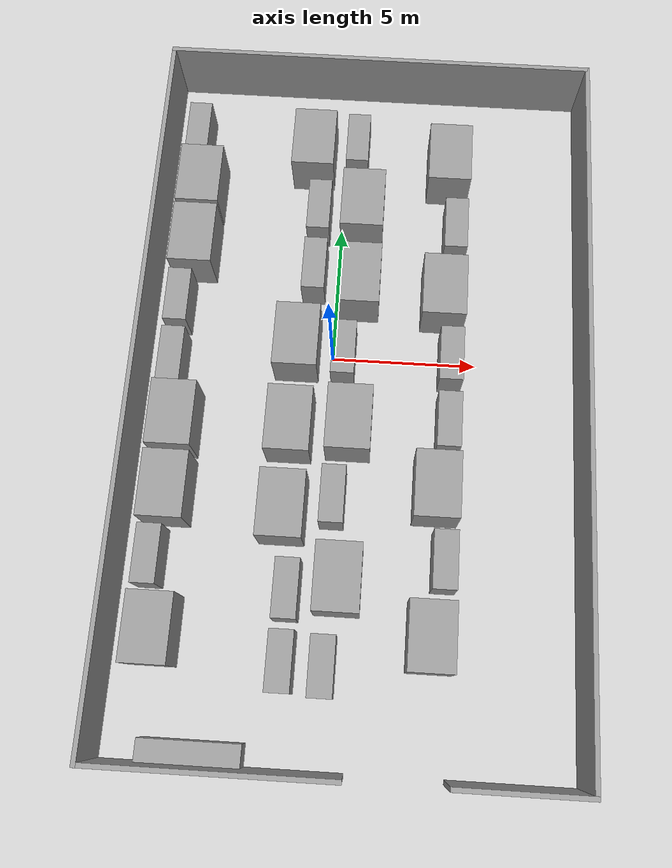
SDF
<sdf version="1.6">
 <world name="default">
  <light name="sun" type="directional">
   <pose>0 0 10 0 -0 0</pose>
   <diffuse>0.8 0.8 0.8 1</diffuse>
   <specular>0.1 0.1 0.1 1</specular>
   <attenuation>
    <range>1000</range>
    <constant>0.9</constant>
    <linear>0.01</linear>
    <quadratic>0.001</quadratic>
   </attenuation>
   <direction>-0.5 0.5 -1</direction>
  </light>
  <model name="ground_plane">
   <static>1</static>
   <link name="link">
    <collision name="collision">
     <geometry><plane><normal>0 0 1</normal><size>100 100</size></plane></geometry>
     <surface><friction><ode><mu>100</mu><mu2>50</mu2></ode></friction></surface>
    </collision>
    <visual name="visual">
     <cast_shadows>0</cast_shadows>
     <geometry><plane><normal>0 0 1</normal><size>100 100</size></plane></geometry>
     <material>
      <script><uri>file://media/materials/scripts/gazebo.material</uri><name>Gazebo/Grey</name></script>
     </material>
    </visual>
   </link>
  </model>
  <gravity>0 0 -9.8</gravity>
  <magnetic_field>6e-06 2.3e-05 -4.2e-05</magnetic_field>
  <atmosphere type="adiabatic"/>
  <physics name="default_physics" default="0" type="ode">
   <max_step_size>0.001</max_step_size>
   <real_time_factor>1</real_time_factor>
   <real_time_update_rate>1000</real_time_update_rate>
  </physics>
  <scene><ambient>0.4 0.4 0.4 1</ambient><background>0.7 0.7 0.7 1</background><shadows>1</shadows></scene>
  <spherical_coordinates>
   <surface_model>EARTH_WGS84</surface_model>
   <latitude_deg>0</latitude_deg>
   <longitude_deg>0</longitude_deg>
   <elevation>0</elevation>
   <heading_deg>0</heading_deg>
  </spherical_coordinates>
  <model name="Machine_08x19">
   <link name="link_1">
    <pose>0 0 0.95 0 -0 0</pose>
    <inertial>
     <mass>1000</mass>
     <inertia><ixx>488.333</ixx><ixy>0</ixy><ixz>0</ixz><iyy>240.833</iyy><iyz>0</iyz><izz>354.167</izz></inertia>
    </inertial>
    <visual name="visual">
     <geometry><box><size>0.8 1.9 1.5</size></box></geometry>
     <material>
      <lighting>1</lighting>
      <script><uri>file://media/materials/scripts/gazebo.material</uri><name>Gazebo/Grey</name></script>
      <ambient>0.3 0.3 0.3 1</ambient>
      <diffuse>0.7 0.7 0.7 1</diffuse>
      <specular>0.01 0.01 0.01 1</specular>
      <emissive>0 0 0 1</emissive>
      <shader type="vertex"><normal_map>__default__</normal_map></shader>
     </material>
    </visual>
    <collision name="collision">
     <geometry><box><size>0.8 1.9 1.5</size></box></geometry>
     <surface>
      <friction>
       <ode><mu>1</mu><mu2>1</mu2><fdir1>0 0 0</fdir1><slip1>0</slip1><slip2>0</slip2></ode>
       <torsional>
        <coefficient>1</coefficient>
        <patch_radius>0</patch_radius>
        <surface_radius>0</surface_radius>
        <use_patch_radius>1</use_patch_radius>
        <ode><slip>0</slip></ode>
       </torsional>
      </friction>
      <bounce><restitution_coefficient>0</restitution_coefficient><threshold>1e+06</threshold></bounce>
      <contact>
       <collide_without_contact>0</collide_without_contact>
       <collide_without_contact_bitmask>1</collide_without_contact_bitmask>
       <collide_bitmask>1</collide_bitmask>
       <ode>
        <soft_cfm>0</soft_cfm>
        <soft_erp>0.2</soft_erp>
        <kp>1e+13</kp>
        <kd>1</kd>
        <max_vel>0.01</max_vel>
        <min_depth>0</min_depth>
       </ode>
       <bullet>
        <split_impulse>1</split_impulse>
        <split_impulse_penetration_threshold>-0.01</split_impulse_penetration_threshold>
        <soft_cfm>0</soft_cfm>
        <soft_erp>0.2</soft_erp>
        <kp>1e+13</kp>
        <kd>1</kd>
       </bullet>
      </contact>
     </surface>
    </collision>
   </link>
   <static>0</static>
   <pose>0.405714 -0.010713 -0.2 0 -0 0</pose>
  </model>
  <model name="Machine_15x22">
   <link name="link_1">
    <inertial>
     <mass>1000</mass>
     <inertia><ixx>704.167</ixx><ixy>0</ixy><ixz>0</ixz><iyy>488.333</iyy><iyz>0</iyz><izz>590.833</izz></inertia>
    </inertial>
    <visual name="visual">
     <geometry><box><size>1.5 2.2 1.9</size></box></geometry>
     <material>
      <lighting>1</lighting>
      <script><uri>file://media/materials/scripts/gazebo.material</uri><name>Gazebo/Grey</name></script>
      <ambient>0.3 0.3 0.3 1</ambient>
      <diffuse>0.7 0.7 0.7 1</diffuse>
      <specular>0.01 0.01 0.01 1</specular>
      <emissive>0 0 0 1</emissive>
      <shader type="vertex"><normal_map>__default__</normal_map></shader>
     </material>
    </visual>
    <collision name="collision">
     <geometry><box><size>1.5 2.2 1.9</size></box></geometry>
     <surface>
      <friction>
       <ode><mu>1</mu><mu2>1</mu2><fdir1>0 0 0</fdir1><slip1>0</slip1><slip2>0</slip2></ode>
       <torsional>
        <coefficient>1</coefficient>
        <patch_radius>0</patch_radius>
        <surface_radius>0</surface_radius>
        <use_patch_radius>1</use_patch_radius>
        <ode><slip>0</slip></ode>
       </torsional>
      </friction>
      <bounce><restitution_coefficient>0</restitution_coefficient><threshold>1e+06</threshold></bounce>
      <contact>
       <collide_without_contact>0</collide_without_contact>
       <collide_without_contact_bitmask>1</collide_without_contact_bitmask>
       <collide_bitmask>1</collide_bitmask>
       <ode>
        <soft_cfm>0</soft_cfm>
        <soft_erp>0.2</soft_erp>
        <kp>1e+13</kp>
        <kd>1</kd>
        <max_vel>0.01</max_vel>
        <min_depth>0</min_depth>
       </ode>
       <bullet>
        <split_impulse>1</split_impulse>
        <split_impulse_penetration_threshold>-0.01</split_impulse_penetration_threshold>
        <soft_cfm>0</soft_cfm>
        <soft_erp>0.2</soft_erp>
        <kp>1e+13</kp>
        <kd>1</kd>
       </bullet>
      </contact>
     </surface>
    </collision>
   </link>
   <static>0</static>
   <pose>0.76024 2.59177 0.95 0 -0 0</pose>
  </model>
  <model name="Machine_15x22_clone">
   <link name="link_1">
    <inertial>
     <mass>1000</mass>
     <inertia><ixx>704.167</ixx><ixy>0</ixy><ixz>0</ixz><iyy>488.333</iyy><iyz>0</iyz><izz>590.833</izz></inertia>
    </inertial>
    <visual name="visual">
     <geometry><box><size>1.5 2.2 1.9</size></box></geometry>
     <material>
      <lighting>1</lighting>
      <script><uri>file://media/materials/scripts/gazebo.material</uri><name>Gazebo/Grey</name></script>
      <ambient>0.3 0.3 0.3 1</ambient>
      <diffuse>0.7 0.7 0.7 1</diffuse>
      <specular>0.01 0.01 0.01 1</specular>
      <emissive>0 0 0 1</emissive>
      <shader type="vertex"><normal_map>__default__</normal_map></shader>
     </material>
    </visual>
    <collision name="collision">
     <geometry><box><size>1.5 2.2 1.9</size></box></geometry>
     <surface>
      <friction>
       <ode><mu>1</mu><mu2>1</mu2><fdir1>0 0 0</fdir1><slip1>0</slip1><slip2>0</slip2></ode>
       <torsional>
        <coefficient>1</coefficient>
        <patch_radius>0</patch_radius>
        <surface_radius>0</surface_radius>
        <use_patch_radius>1</use_patch_radius>
        <ode><slip>0</slip></ode>
       </torsional>
      </friction>
      <bounce><restitution_coefficient>0</restitution_coefficient><threshold>1e+06</threshold></bounce>
      <contact>
       <collide_without_contact>0</collide_without_contact>
       <collide_without_contact_bitmask>1</collide_without_contact_bitmask>
       <collide_bitmask>1</collide_bitmask>
       <ode>
        <soft_cfm>0</soft_cfm>
        <soft_erp>0.2</soft_erp>
        <kp>1e+13</kp>
        <kd>1</kd>
        <max_vel>0.01</max_vel>
        <min_depth>0</min_depth>
       </ode>
       <bullet>
        <split_impulse>1</split_impulse>
        <split_impulse_penetration_threshold>-0.01</split_impulse_penetration_threshold>
        <soft_cfm>0</soft_cfm>
        <soft_erp>0.2</soft_erp>
        <kp>1e+13</kp>
        <kd>1</kd>
       </bullet>
      </contact>
     </surface>
    </collision>
   </link>
   <static>0</static>
   <pose>0.750153 -2.5576 0.95 0 -0 0</pose>
  </model>
  <model name="Machine_15x22_clone_clone">
   <link name="link_1">
    <inertial>
     <mass>1000</mass>
     <inertia><ixx>704.167</ixx><ixy>0</ixy><ixz>0</ixz><iyy>488.333</iyy><iyz>0</iyz><izz>590.833</izz></inertia>
    </inertial>
    <visual name="visual">
     <geometry><box><size>1.5 2.2 1.9</size></box></geometry>
     <material>
      <lighting>1</lighting>
      <script><uri>file://media/materials/scripts/gazebo.material</uri><name>Gazebo/Grey</name></script>
      <ambient>0.3 0.3 0.3 1</ambient>
      <diffuse>0.7 0.7 0.7 1</diffuse>
      <specular>0.01 0.01 0.01 1</specular>
      <emissive>0 0 0 1</emissive>
      <shader type="vertex"><normal_map>__default__</normal_map></shader>
     </material>
    </visual>
    <collision name="collision">
     <geometry><box><size>1.5 2.2 1.9</size></box></geometry>
     <surface>
      <friction>
       <ode><mu>1</mu><mu2>1</mu2><fdir1>0 0 0</fdir1><slip1>0</slip1><slip2>0</slip2></ode>
       <torsional>
        <coefficient>1</coefficient>
        <patch_radius>0</patch_radius>
        <surface_radius>0</surface_radius>
        <use_patch_radius>1</use_patch_radius>
        <ode><slip>0</slip></ode>
       </torsional>
      </friction>
      <bounce><restitution_coefficient>0</restitution_coefficient><threshold>1e+06</threshold></bounce>
      <contact>
       <collide_without_contact>0</collide_without_contact>
       <collide_without_contact_bitmask>1</collide_without_contact_bitmask>
       <collide_bitmask>1</collide_bitmask>
       <ode>
        <soft_cfm>0</soft_cfm>
        <soft_erp>0.2</soft_erp>
        <kp>1e+13</kp>
        <kd>1</kd>
        <max_vel>0.01</max_vel>
        <min_depth>0</min_depth>
       </ode>
       <bullet>
        <split_impulse>1</split_impulse>
        <split_impulse_penetration_threshold>-0.01</split_impulse_penetration_threshold>
        <soft_cfm>0</soft_cfm>
        <soft_erp>0.2</soft_erp>
        <kp>1e+13</kp>
        <kd>1</kd>
       </bullet>
      </contact>
     </surface>
    </collision>
   </link>
   <static>0</static>
   <pose>-1.22648 -2.71999 0.95 0 -0 0</pose>
  </model>
  <model name="Machine_15x22_clone_clone_0">
   <link name="link_1">
    <inertial>
     <mass>1000</mass>
     <inertia><ixx>704.167</ixx><ixy>0</ixy><ixz>0</ixz><iyy>488.333</iyy><iyz>0</iyz><izz>590.833</izz></inertia>
    </inertial>
    <visual name="visual">
     <geometry><box><size>1.5 2.2 1.9</size></box></geometry>
     <material>
      <lighting>1</lighting>
      <script><uri>file://media/materials/scripts/gazebo.material</uri><name>Gazebo/Grey</name></script>
      <ambient>0.3 0.3 0.3 1</ambient>
      <diffuse>0.7 0.7 0.7 1</diffuse>
      <specular>0.01 0.01 0.01 1</specular>
      <emissive>0 0 0 1</emissive>
      <shader type="vertex"><normal_map>__default__</normal_map></shader>
     </material>
    </visual>
    <collision name="collision">
     <geometry><box><size>1.5 2.2 1.9</size></box></geometry>
     <surface>
      <friction>
       <ode><mu>1</mu><mu2>1</mu2><fdir1>0 0 0</fdir1><slip1>0</slip1><slip2>0</slip2></ode>
       <torsional>
        <coefficient>1</coefficient>
        <patch_radius>0</patch_radius>
        <surface_radius>0</surface_radius>
        <use_patch_radius>1</use_patch_radius>
        <ode><slip>0</slip></ode>
       </torsional>
      </friction>
      <bounce><restitution_coefficient>0</restitution_coefficient><threshold>1e+06</threshold></bounce>
      <contact>
       <collide_without_contact>0</collide_without_contact>
       <collide_without_contact_bitmask>1</collide_without_contact_bitmask>
       <collide_bitmask>1</collide_bitmask>
       <ode>
        <soft_cfm>0</soft_cfm>
        <soft_erp>0.2</soft_erp>
        <kp>1e+13</kp>
        <kd>1</kd>
        <max_vel>0.01</max_vel>
        <min_depth>0</min_depth>
       </ode>
       <bullet>
        <split_impulse>1</split_impulse>
        <split_impulse_penetration_threshold>-0.01</split_impulse_penetration_threshold>
        <soft_cfm>0</soft_cfm>
        <soft_erp>0.2</soft_erp>
        <kp>1e+13</kp>
        <kd>1</kd>
       </bullet>
      </contact>
     </surface>
    </collision>
   </link>
   <static>0</static>
   <pose>-1.19751 0.209867 0.95 0 -0 0</pose>
  </model>
  <model name="Machine_15x22_clone_clone_1">
   <link name="link_1">
    <inertial>
     <mass>1000</mass>
     <inertia><ixx>704.167</ixx><ixy>0</ixy><ixz>0</ixz><iyy>488.333</iyy><iyz>0</iyz><izz>590.833</izz></inertia>
    </inertial>
    <visual name="visual">
     <geometry><box><size>1.5 2.2 1.9</size></box></geometry>
     <material>
      <lighting>1</lighting>
      <script><uri>file://media/materials/scripts/gazebo.material</uri><name>Gazebo/Grey</name></script>
      <ambient>0.3 0.3 0.3 1</ambient>
      <diffuse>0.7 0.7 0.7 1</diffuse>
      <specular>0.01 0.01 0.01 1</specular>
      <emissive>0 0 0 1</emissive>
      <shader type="vertex"><normal_map>__default__</normal_map></shader>
     </material>
    </visual>
    <collision name="collision">
     <geometry><box><size>1.5 2.2 1.9</size></box></geometry>
     <surface>
      <friction>
       <ode><mu>1</mu><mu2>1</mu2><fdir1>0 0 0</fdir1><slip1>0</slip1><slip2>0</slip2></ode>
       <torsional>
        <coefficient>1</coefficient>
        <patch_radius>0</patch_radius>
        <surface_radius>0</surface_radius>
        <use_patch_radius>1</use_patch_radius>
        <ode><slip>0</slip></ode>
       </torsional>
      </friction>
      <bounce><restitution_coefficient>0</restitution_coefficient><threshold>1e+06</threshold></bounce>
      <contact>
       <collide_without_contact>0</collide_without_contact>
       <collide_without_contact_bitmask>1</collide_without_contact_bitmask>
       <collide_bitmask>1</collide_bitmask>
       <ode>
        <soft_cfm>0</soft_cfm>
        <soft_erp>0.2</soft_erp>
        <kp>1e+13</kp>
        <kd>1</kd>
        <max_vel>0.01</max_vel>
        <min_depth>0</min_depth>
       </ode>
       <bullet>
        <split_impulse>1</split_impulse>
        <split_impulse_penetration_threshold>-0.01</split_impulse_penetration_threshold>
        <soft_cfm>0</soft_cfm>
        <soft_erp>0.2</soft_erp>
        <kp>1e+13</kp>
        <kd>1</kd>
       </bullet>
      </contact>
     </surface>
    </collision>
   </link>
   <static>0</static>
   <pose>-1.23882 -5.53494 0.95 0 -0 0</pose>
  </model>
  <model name="Machine_15x22_clone_clone_2">
   <link name="link_1">
    <inertial>
     <mass>1000</mass>
     <inertia><ixx>704.167</ixx><ixy>0</ixy><ixz>0</ixz><iyy>488.333</iyy><iyz>0</iyz><izz>590.833</izz></inertia>
    </inertial>
    <visual name="visual">
     <geometry><box><size>1.5 2.2 1.9</size></box></geometry>
     <material>
      <lighting>1</lighting>
      <script><uri>file://media/materials/scripts/gazebo.material</uri><name>Gazebo/Grey</name></script>
      <ambient>0.3 0.3 0.3 1</ambient>
      <diffuse>0.7 0.7 0.7 1</diffuse>
      <specular>0.01 0.01 0.01 1</specular>
      <emissive>0 0 0 1</emissive>
      <shader type="vertex"><normal_map>__default__</normal_map></shader>
     </material>
    </visual>
    <collision name="collision">
     <geometry><box><size>1.5 2.2 1.9</size></box></geometry>
     <surface>
      <friction>
       <ode><mu>1</mu><mu2>1</mu2><fdir1>0 0 0</fdir1><slip1>0</slip1><slip2>0</slip2></ode>
       <torsional>
        <coefficient>1</coefficient>
        <patch_radius>0</patch_radius>
        <surface_radius>0</surface_radius>
        <use_patch_radius>1</use_patch_radius>
        <ode><slip>0</slip></ode>
       </torsional>
      </friction>
      <bounce><restitution_coefficient>0</restitution_coefficient><threshold>1e+06</threshold></bounce>
      <contact>
       <collide_without_contact>0</collide_without_contact>
       <collide_without_contact_bitmask>1</collide_without_contact_bitmask>
       <collide_bitmask>1</collide_bitmask>
       <ode>
        <soft_cfm>0</soft_cfm>
        <soft_erp>0.2</soft_erp>
        <kp>1e+13</kp>
        <kd>1</kd>
        <max_vel>0.01</max_vel>
        <min_depth>0</min_depth>
       </ode>
       <bullet>
        <split_impulse>1</split_impulse>
        <split_impulse_penetration_threshold>-0.01</split_impulse_penetration_threshold>
        <soft_cfm>0</soft_cfm>
        <soft_erp>0.2</soft_erp>
        <kp>1e+13</kp>
        <kd>1</kd>
       </bullet>
      </contact>
     </surface>
    </collision>
   </link>
   <static>0</static>
   <pose>0.722114 -7.73998 0.95 0 -0 0</pose>
  </model>
  <model name="Machine_15x22_clone_clone_3">
   <link name="link_1">
    <inertial>
     <mass>1000</mass>
     <inertia><ixx>704.167</ixx><ixy>0</ixy><ixz>0</ixz><iyy>488.333</iyy><iyz>0</iyz><izz>590.833</izz></inertia>
    </inertial>
    <visual name="visual">
     <geometry><box><size>1.5 2.2 1.9</size></box></geometry>
     <material>
      <lighting>1</lighting>
      <script><uri>file://media/materials/scripts/gazebo.material</uri><name>Gazebo/Grey</name></script>
      <ambient>0.3 0.3 0.3 1</ambient>
      <diffuse>0.7 0.7 0.7 1</diffuse>
      <specular>0.01 0.01 0.01 1</specular>
      <emissive>0 0 0 1</emissive>
      <shader type="vertex"><normal_map>__default__</normal_map></shader>
     </material>
    </visual>
    <collision name="collision">
     <geometry><box><size>1.5 2.2 1.9</size></box></geometry>
     <surface>
      <friction>
       <ode><mu>1</mu><mu2>1</mu2><fdir1>0 0 0</fdir1><slip1>0</slip1><slip2>0</slip2></ode>
       <torsional>
        <coefficient>1</coefficient>
        <patch_radius>0</patch_radius>
        <surface_radius>0</surface_radius>
        <use_patch_radius>1</use_patch_radius>
        <ode><slip>0</slip></ode>
       </torsional>
      </friction>
      <bounce><restitution_coefficient>0</restitution_coefficient><threshold>1e+06</threshold></bounce>
      <contact>
       <collide_without_contact>0</collide_without_contact>
       <collide_without_contact_bitmask>1</collide_without_contact_bitmask>
       <collide_bitmask>1</collide_bitmask>
       <ode>
        <soft_cfm>0</soft_cfm>
        <soft_erp>0.2</soft_erp>
        <kp>1e+13</kp>
        <kd>1</kd>
        <max_vel>0.01</max_vel>
        <min_depth>0</min_depth>
       </ode>
       <bullet>
        <split_impulse>1</split_impulse>
        <split_impulse_penetration_threshold>-0.01</split_impulse_penetration_threshold>
        <soft_cfm>0</soft_cfm>
        <soft_erp>0.2</soft_erp>
        <kp>1e+13</kp>
        <kd>1</kd>
       </bullet>
      </contact>
     </surface>
    </collision>
   </link>
   <static>0</static>
   <pose>0.741989 5.47826 0.95 0 -0 0</pose>
  </model>
  <model name="Machine_15x22_clone_clone_4">
   <link name="link_1">
    <inertial>
     <mass>1000</mass>
     <inertia><ixx>704.167</ixx><ixy>0</ixy><ixz>0</ixz><iyy>488.333</iyy><iyz>0</iyz><izz>590.833</izz></inertia>
    </inertial>
    <visual name="visual">
     <geometry><box><size>1.5 2.2 1.9</size></box></geometry>
     <material>
      <lighting>1</lighting>
      <script><uri>file://media/materials/scripts/gazebo.material</uri><name>Gazebo/Grey</name></script>
      <ambient>0.3 0.3 0.3 1</ambient>
      <diffuse>0.7 0.7 0.7 1</diffuse>
      <specular>0.01 0.01 0.01 1</specular>
      <emissive>0 0 0 1</emissive>
      <shader type="vertex"><normal_map>__default__</normal_map></shader>
     </material>
    </visual>
    <collision name="collision">
     <geometry><box><size>1.5 2.2 1.9</size></box></geometry>
     <surface>
      <friction>
       <ode><mu>1</mu><mu2>1</mu2><fdir1>0 0 0</fdir1><slip1>0</slip1><slip2>0</slip2></ode>
       <torsional>
        <coefficient>1</coefficient>
        <patch_radius>0</patch_radius>
        <surface_radius>0</surface_radius>
        <use_patch_radius>1</use_patch_radius>
        <ode><slip>0</slip></ode>
       </torsional>
      </friction>
      <bounce><restitution_coefficient>0</restitution_coefficient><threshold>1e+06</threshold></bounce>
      <contact>
       <collide_without_contact>0</collide_without_contact>
       <collide_without_contact_bitmask>1</collide_without_contact_bitmask>
       <collide_bitmask>1</collide_bitmask>
       <ode>
        <soft_cfm>0</soft_cfm>
        <soft_erp>0.2</soft_erp>
        <kp>1e+13</kp>
        <kd>1</kd>
        <max_vel>0.01</max_vel>
        <min_depth>0</min_depth>
       </ode>
       <bullet>
        <split_impulse>1</split_impulse>
        <split_impulse_penetration_threshold>-0.01</split_impulse_penetration_threshold>
        <soft_cfm>0</soft_cfm>
        <soft_erp>0.2</soft_erp>
        <kp>1e+13</kp>
        <kd>1</kd>
       </bullet>
      </contact>
     </surface>
    </collision>
   </link>
   <static>0</static>
   <pose>-5.06342 -5.13057 0.95 0 -0 0</pose>
  </model>
  <model name="Machine_15x22_clone_clone_5">
   <link name="link_1">
    <inertial>
     <mass>1000</mass>
     <inertia><ixx>704.167</ixx><ixy>0</ixy><ixz>0</ixz><iyy>488.333</iyy><iyz>0</iyz><izz>590.833</izz></inertia>
    </inertial>
    <visual name="visual">
     <geometry><box><size>1.5 2.2 1.9</size></box></geometry>
     <material>
      <lighting>1</lighting>
      <script><uri>file://media/materials/scripts/gazebo.material</uri><name>Gazebo/Grey</name></script>
      <ambient>0.3 0.3 0.3 1</ambient>
      <diffuse>0.7 0.7 0.7 1</diffuse>
      <specular>0.01 0.01 0.01 1</specular>
      <emissive>0 0 0 1</emissive>
      <shader type="vertex"><normal_map>__default__</normal_map></shader>
     </material>
    </visual>
    <collision name="collision">
     <geometry><box><size>1.5 2.2 1.9</size></box></geometry>
     <surface>
      <friction>
       <ode><mu>1</mu><mu2>1</mu2><fdir1>0 0 0</fdir1><slip1>0</slip1><slip2>0</slip2></ode>
       <torsional>
        <coefficient>1</coefficient>
        <patch_radius>0</patch_radius>
        <surface_radius>0</surface_radius>
        <use_patch_radius>1</use_patch_radius>
        <ode><slip>0</slip></ode>
       </torsional>
      </friction>
      <bounce><restitution_coefficient>0</restitution_coefficient><threshold>1e+06</threshold></bounce>
      <contact>
       <collide_without_contact>0</collide_without_contact>
       <collide_without_contact_bitmask>1</collide_without_contact_bitmask>
       <collide_bitmask>1</collide_bitmask>
       <ode>
        <soft_cfm>0</soft_cfm>
        <soft_erp>0.2</soft_erp>
        <kp>1e+13</kp>
        <kd>1</kd>
        <max_vel>0.01</max_vel>
        <min_depth>0</min_depth>
       </ode>
       <bullet>
        <split_impulse>1</split_impulse>
        <split_impulse_penetration_threshold>-0.01</split_impulse_penetration_threshold>
        <soft_cfm>0</soft_cfm>
        <soft_erp>0.2</soft_erp>
        <kp>1e+13</kp>
        <kd>1</kd>
       </bullet>
      </contact>
     </surface>
    </collision>
   </link>
   <static>0</static>
   <pose>-5.08331 -2.75437 0.95 0 -0 0</pose>
  </model>
  <model name="Machine_15x22_clone_clone_6">
   <link name="link_1">
    <inertial>
     <mass>1000</mass>
     <inertia><ixx>704.167</ixx><ixy>0</ixy><ixz>0</ixz><iyy>488.333</iyy><iyz>0</iyz><izz>590.833</izz></inertia>
    </inertial>
    <visual name="visual">
     <geometry><box><size>1.5 2.2 1.9</size></box></geometry>
     <material>
      <lighting>1</lighting>
      <script><uri>file://media/materials/scripts/gazebo.material</uri><name>Gazebo/Grey</name></script>
      <ambient>0.3 0.3 0.3 1</ambient>
      <diffuse>0.7 0.7 0.7 1</diffuse>
      <specular>0.01 0.01 0.01 1</specular>
      <emissive>0 0 0 1</emissive>
      <shader type="vertex"><normal_map>__default__</normal_map></shader>
     </material>
    </visual>
    <collision name="collision">
     <geometry><box><size>1.5 2.2 1.9</size></box></geometry>
     <surface>
      <friction>
       <ode><mu>1</mu><mu2>1</mu2><fdir1>0 0 0</fdir1><slip1>0</slip1><slip2>0</slip2></ode>
       <torsional>
        <coefficient>1</coefficient>
        <patch_radius>0</patch_radius>
        <surface_radius>0</surface_radius>
        <use_patch_radius>1</use_patch_radius>
        <ode><slip>0</slip></ode>
       </torsional>
      </friction>
      <bounce><restitution_coefficient>0</restitution_coefficient><threshold>1e+06</threshold></bounce>
      <contact>
       <collide_without_contact>0</collide_without_contact>
       <collide_without_contact_bitmask>1</collide_without_contact_bitmask>
       <collide_bitmask>1</collide_bitmask>
       <ode>
        <soft_cfm>0</soft_cfm>
        <soft_erp>0.2</soft_erp>
        <kp>1e+13</kp>
        <kd>1</kd>
        <max_vel>0.01</max_vel>
        <min_depth>0</min_depth>
       </ode>
       <bullet>
        <split_impulse>1</split_impulse>
        <split_impulse_penetration_threshold>-0.01</split_impulse_penetration_threshold>
        <soft_cfm>0</soft_cfm>
        <soft_erp>0.2</soft_erp>
        <kp>1e+13</kp>
        <kd>1</kd>
       </bullet>
      </contact>
     </surface>
    </collision>
   </link>
   <static>0</static>
   <pose>-5.11143 3.77632 0.95 0 -0 0</pose>
  </model>
  <model name="Machine_15x22_clone_clone_7">
   <link name="link_1">
    <inertial>
     <mass>1000</mass>
     <inertia><ixx>704.167</ixx><ixy>0</ixy><ixz>0</ixz><iyy>488.333</iyy><iyz>0</iyz><izz>590.833</izz></inertia>
    </inertial>
    <visual name="visual">
     <geometry><box><size>1.5 2.2 1.9</size></box></geometry>
     <material>
      <lighting>1</lighting>
      <script><uri>file://media/materials/scripts/gazebo.material</uri><name>Gazebo/Grey</name></script>
      <ambient>0.3 0.3 0.3 1</ambient>
      <diffuse>0.7 0.7 0.7 1</diffuse>
      <specular>0.01 0.01 0.01 1</specular>
      <emissive>0 0 0 1</emissive>
      <shader type="vertex"><normal_map>__default__</normal_map></shader>
     </material>
    </visual>
    <collision name="collision">
     <geometry><box><size>1.5 2.2 1.9</size></box></geometry>
     <surface>
      <friction>
       <ode><mu>1</mu><mu2>1</mu2><fdir1>0 0 0</fdir1><slip1>0</slip1><slip2>0</slip2></ode>
       <torsional>
        <coefficient>1</coefficient>
        <patch_radius>0</patch_radius>
        <surface_radius>0</surface_radius>
        <use_patch_radius>1</use_patch_radius>
        <ode><slip>0</slip></ode>
       </torsional>
      </friction>
      <bounce><restitution_coefficient>0</restitution_coefficient><threshold>1e+06</threshold></bounce>
      <contact>
       <collide_without_contact>0</collide_without_contact>
       <collide_without_contact_bitmask>1</collide_without_contact_bitmask>
       <collide_bitmask>1</collide_bitmask>
       <ode>
        <soft_cfm>0</soft_cfm>
        <soft_erp>0.2</soft_erp>
        <kp>1e+13</kp>
        <kd>1</kd>
        <max_vel>0.01</max_vel>
        <min_depth>0</min_depth>
       </ode>
       <bullet>
        <split_impulse>1</split_impulse>
        <split_impulse_penetration_threshold>-0.01</split_impulse_penetration_threshold>
        <soft_cfm>0</soft_cfm>
        <soft_erp>0.2</soft_erp>
        <kp>1e+13</kp>
        <kd>1</kd>
       </bullet>
      </contact>
     </surface>
    </collision>
   </link>
   <static>0</static>
   <pose>3.74745 -9.35966 0.95 0 -0 0</pose>
  </model>
  <model name="Machine_15x22_clone_clone_8">
   <link name="link_1">
    <inertial>
     <mass>1000</mass>
     <inertia><ixx>704.167</ixx><ixy>0</ixy><ixz>0</ixz><iyy>488.333</iyy><iyz>0</iyz><izz>590.833</izz></inertia>
    </inertial>
    <visual name="visual">
     <geometry><box><size>1.5 2.2 1.9</size></box></geometry>
     <material>
      <lighting>1</lighting>
      <script><uri>file://media/materials/scripts/gazebo.material</uri><name>Gazebo/Grey</name></script>
      <ambient>0.3 0.3 0.3 1</ambient>
      <diffuse>0.7 0.7 0.7 1</diffuse>
      <specular>0.01 0.01 0.01 1</specular>
      <emissive>0 0 0 1</emissive>
      <shader type="vertex"><normal_map>__default__</normal_map></shader>
     </material>
    </visual>
    <collision name="collision">
     <geometry><box><size>1.5 2.2 1.9</size></box></geometry>
     <surface>
      <friction>
       <ode><mu>1</mu><mu2>1</mu2><fdir1>0 0 0</fdir1><slip1>0</slip1><slip2>0</slip2></ode>
       <torsional>
        <coefficient>1</coefficient>
        <patch_radius>0</patch_radius>
        <surface_radius>0</surface_radius>
        <use_patch_radius>1</use_patch_radius>
        <ode><slip>0</slip></ode>
       </torsional>
      </friction>
      <bounce><restitution_coefficient>0</restitution_coefficient><threshold>1e+06</threshold></bounce>
      <contact>
       <collide_without_contact>0</collide_without_contact>
       <collide_without_contact_bitmask>1</collide_without_contact_bitmask>
       <collide_bitmask>1</collide_bitmask>
       <ode>
        <soft_cfm>0</soft_cfm>
        <soft_erp>0.2</soft_erp>
        <kp>1e+13</kp>
        <kd>1</kd>
        <max_vel>0.01</max_vel>
        <min_depth>0</min_depth>
       </ode>
       <bullet>
        <split_impulse>1</split_impulse>
        <split_impulse_penetration_threshold>-0.01</split_impulse_penetration_threshold>
        <soft_cfm>0</soft_cfm>
        <soft_erp>0.2</soft_erp>
        <kp>1e+13</kp>
        <kd>1</kd>
       </bullet>
      </contact>
     </surface>
    </collision>
   </link>
   <static>0</static>
   <pose>3.75078 -4.62113 0.95 0 -0 0</pose>
  </model>
  <model name="Machine_15x22_clone_clone_9">
   <link name="link_1">
    <inertial>
     <mass>1000</mass>
     <inertia><ixx>704.167</ixx><ixy>0</ixy><ixz>0</ixz><iyy>488.333</iyy><iyz>0</iyz><izz>590.833</izz></inertia>
    </inertial>
    <visual name="visual">
     <geometry><box><size>1.5 2.2 1.9</size></box></geometry>
     <material>
      <lighting>1</lighting>
      <script><uri>file://media/materials/scripts/gazebo.material</uri><name>Gazebo/Grey</name></script>
      <ambient>0.3 0.3 0.3 1</ambient>
      <diffuse>0.7 0.7 0.7 1</diffuse>
      <specular>0.01 0.01 0.01 1</specular>
      <emissive>0 0 0 1</emissive>
      <shader type="vertex"><normal_map>__default__</normal_map></shader>
     </material>
    </visual>
    <collision name="collision">
     <geometry><box><size>1.5 2.2 1.9</size></box></geometry>
     <surface>
      <friction>
       <ode><mu>1</mu><mu2>1</mu2><fdir1>0 0 0</fdir1><slip1>0</slip1><slip2>0</slip2></ode>
       <torsional>
        <coefficient>1</coefficient>
        <patch_radius>0</patch_radius>
        <surface_radius>0</surface_radius>
        <use_patch_radius>1</use_patch_radius>
        <ode><slip>0</slip></ode>
       </torsional>
      </friction>
      <bounce><restitution_coefficient>0</restitution_coefficient><threshold>1e+06</threshold></bounce>
      <contact>
       <collide_without_contact>0</collide_without_contact>
       <collide_without_contact_bitmask>1</collide_without_contact_bitmask>
       <collide_bitmask>1</collide_bitmask>
       <ode>
        <soft_cfm>0</soft_cfm>
        <soft_erp>0.2</soft_erp>
        <kp>1e+13</kp>
        <kd>1</kd>
        <max_vel>0.01</max_vel>
        <min_depth>0</min_depth>
       </ode>
       <bullet>
        <split_impulse>1</split_impulse>
        <split_impulse_penetration_threshold>-0.01</split_impulse_penetration_threshold>
        <soft_cfm>0</soft_cfm>
        <soft_erp>0.2</soft_erp>
        <kp>1e+13</kp>
        <kd>1</kd>
       </bullet>
      </contact>
     </surface>
    </collision>
   </link>
   <static>0</static>
   <pose>3.74714 2.32081 0.95 0 -0 0</pose>
  </model>
  <model name="Machine_15x22_clone_clone_10">
   <link name="link_1">
    <inertial>
     <mass>1000</mass>
     <inertia><ixx>704.167</ixx><ixy>0</ixy><ixz>0</ixz><iyy>488.333</iyy><iyz>0</iyz><izz>590.833</izz></inertia>
    </inertial>
    <visual name="visual">
     <geometry><box><size>1.5 2.2 1.9</size></box></geometry>
     <material>
      <lighting>1</lighting>
      <script><uri>file://media/materials/scripts/gazebo.material</uri><name>Gazebo/Grey</name></script>
      <ambient>0.3 0.3 0.3 1</ambient>
      <diffuse>0.7 0.7 0.7 1</diffuse>
      <specular>0.01 0.01 0.01 1</specular>
      <emissive>0 0 0 1</emissive>
      <shader type="vertex"><normal_map>__default__</normal_map></shader>
     </material>
    </visual>
    <collision name="collision">
     <geometry><box><size>1.5 2.2 1.9</size></box></geometry>
     <surface>
      <friction>
       <ode><mu>1</mu><mu2>1</mu2><fdir1>0 0 0</fdir1><slip1>0</slip1><slip2>0</slip2></ode>
       <torsional>
        <coefficient>1</coefficient>
        <patch_radius>0</patch_radius>
        <surface_radius>0</surface_radius>
        <use_patch_radius>1</use_patch_radius>
        <ode><slip>0</slip></ode>
       </torsional>
      </friction>
      <bounce><restitution_coefficient>0</restitution_coefficient><threshold>1e+06</threshold></bounce>
      <contact>
       <collide_without_contact>0</collide_without_contact>
       <collide_without_contact_bitmask>1</collide_without_contact_bitmask>
       <collide_bitmask>1</collide_bitmask>
       <ode>
        <soft_cfm>0</soft_cfm>
        <soft_erp>0.2</soft_erp>
        <kp>1e+13</kp>
        <kd>1</kd>
        <max_vel>0.01</max_vel>
        <min_depth>0</min_depth>
       </ode>
       <bullet>
        <split_impulse>1</split_impulse>
        <split_impulse_penetration_threshold>-0.01</split_impulse_penetration_threshold>
        <soft_cfm>0</soft_cfm>
        <soft_erp>0.2</soft_erp>
        <kp>1e+13</kp>
        <kd>1</kd>
       </bullet>
      </contact>
     </surface>
    </collision>
   </link>
   <static>0</static>
   <pose>3.76584 7.46429 0.95 0 -0 0</pose>
  </model>
  <model name="Machine_08x19_clone">
   <link name="link_1">
    <pose>0 0 0.95 0 -0 0</pose>
    <inertial>
     <mass>1000</mass>
     <inertia><ixx>488.333</ixx><ixy>0</ixy><ixz>0</ixz><iyy>240.833</iyy><iyz>0</iyz><izz>354.167</izz></inertia>
    </inertial>
    <visual name="visual">
     <geometry><box><size>0.8 1.9 1.5</size></box></geometry>
     <material>
      <lighting>1</lighting>
      <script><uri>file://media/materials/scripts/gazebo.material</uri><name>Gazebo/Grey</name></script>
      <ambient>0.3 0.3 0.3 1</ambient>
      <diffuse>0.7 0.7 0.7 1</diffuse>
      <specular>0.01 0.01 0.01 1</specular>
      <emissive>0 0 0 1</emissive>
      <shader type="vertex"><normal_map>__default__</normal_map></shader>
     </material>
    </visual>
    <collision name="collision">
     <geometry><box><size>0.8 1.9 1.5</size></box></geometry>
     <surface>
      <friction>
       <ode><mu>1</mu><mu2>1</mu2><fdir1>0 0 0</fdir1><slip1>0</slip1><slip2>0</slip2></ode>
       <torsional>
        <coefficient>1</coefficient>
        <patch_radius>0</patch_radius>
        <surface_radius>0</surface_radius>
        <use_patch_radius>1</use_patch_radius>
        <ode><slip>0</slip></ode>
       </torsional>
      </friction>
      <bounce><restitution_coefficient>0</restitution_coefficient><threshold>1e+06</threshold></bounce>
      <contact>
       <collide_without_contact>0</collide_without_contact>
       <collide_without_contact_bitmask>1</collide_without_contact_bitmask>
       <collide_bitmask>1</collide_bitmask>
       <ode>
        <soft_cfm>0</soft_cfm>
        <soft_erp>0.2</soft_erp>
        <kp>1e+13</kp>
        <kd>1</kd>
        <max_vel>0.01</max_vel>
        <min_depth>0</min_depth>
       </ode>
       <bullet>
        <split_impulse>1</split_impulse>
        <split_impulse_penetration_threshold>-0.01</split_impulse_penetration_threshold>
        <soft_cfm>0</soft_cfm>
        <soft_erp>0.2</soft_erp>
        <kp>1e+13</kp>
        <kd>1</kd>
       </bullet>
      </contact>
     </surface>
    </collision>
   </link>
   <static>0</static>
   <pose>-5.42861 -0.580294 -0.2 0 -0 0</pose>
  </model>
  <model name="Machine_08x19_clone_0">
   <link name="link_1">
    <pose>0 0 0.95 0 -0 0</pose>
    <inertial>
     <mass>1000</mass>
     <inertia><ixx>488.333</ixx><ixy>0</ixy><ixz>0</ixz><iyy>240.833</iyy><iyz>0</iyz><izz>354.167</izz></inertia>
    </inertial>
    <visual name="visual">
     <geometry><box><size>0.8 1.9 1.5</size></box></geometry>
     <material>
      <lighting>1</lighting>
      <script><uri>file://media/materials/scripts/gazebo.material</uri><name>Gazebo/Grey</name></script>
      <ambient>0.3 0.3 0.3 1</ambient>
      <diffuse>0.7 0.7 0.7 1</diffuse>
      <specular>0.01 0.01 0.01 1</specular>
      <emissive>0 0 0 1</emissive>
      <shader type="vertex"><normal_map>__default__</normal_map></shader>
     </material>
    </visual>
    <collision name="collision">
     <geometry><box><size>0.8 1.9 1.5</size></box></geometry>
     <surface>
      <friction>
       <ode><mu>1</mu><mu2>1</mu2><fdir1>0 0 0</fdir1><slip1>0</slip1><slip2>0</slip2></ode>
       <torsional>
        <coefficient>1</coefficient>
        <patch_radius>0</patch_radius>
        <surface_radius>0</surface_radius>
        <use_patch_radius>1</use_patch_radius>
        <ode><slip>0</slip></ode>
       </torsional>
      </friction>
      <bounce><restitution_coefficient>0</restitution_coefficient><threshold>1e+06</threshold></bounce>
      <contact>
       <collide_without_contact>0</collide_without_contact>
       <collide_without_contact_bitmask>1</collide_without_contact_bitmask>
       <collide_bitmask>1</collide_bitmask>
       <ode>
        <soft_cfm>0</soft_cfm>
        <soft_erp>0.2</soft_erp>
        <kp>1e+13</kp>
        <kd>1</kd>
        <max_vel>0.01</max_vel>
        <min_depth>0</min_depth>
       </ode>
       <bullet>
        <split_impulse>1</split_impulse>
        <split_impulse_penetration_threshold>-0.01</split_impulse_penetration_threshold>
        <soft_cfm>0</soft_cfm>
        <soft_erp>0.2</soft_erp>
        <kp>1e+13</kp>
        <kd>1</kd>
       </bullet>
      </contact>
     </surface>
    </collision>
   </link>
   <static>0</static>
   <pose>-5.4446 1.57197 -0.2 0 -0 0</pose>
  </model>
  <model name="Machine_08x19_clone_1">
   <link name="link_1">
    <pose>0 0 0.95 0 -0 0</pose>
    <inertial>
     <mass>1000</mass>
     <inertia><ixx>488.333</ixx><ixy>0</ixy><ixz>0</ixz><iyy>240.833</iyy><iyz>0</iyz><izz>354.167</izz></inertia>
    </inertial>
    <visual name="visual">
     <geometry><box><size>0.8 1.9 1.5</size></box></geometry>
     <material>
      <lighting>1</lighting>
      <script><uri>file://media/materials/scripts/gazebo.material</uri><name>Gazebo/Grey</name></script>
      <ambient>0.3 0.3 0.3 1</ambient>
      <diffuse>0.7 0.7 0.7 1</diffuse>
      <specular>0.01 0.01 0.01 1</specular>
      <emissive>0 0 0 1</emissive>
      <shader type="vertex"><normal_map>__default__</normal_map></shader>
     </material>
    </visual>
    <collision name="collision">
     <geometry><box><size>0.8 1.9 1.5</size></box></geometry>
     <surface>
      <friction>
       <ode><mu>1</mu><mu2>1</mu2><fdir1>0 0 0</fdir1><slip1>0</slip1><slip2>0</slip2></ode>
       <torsional>
        <coefficient>1</coefficient>
        <patch_radius>0</patch_radius>
        <surface_radius>0</surface_radius>
        <use_patch_radius>1</use_patch_radius>
        <ode><slip>0</slip></ode>
       </torsional>
      </friction>
      <bounce><restitution_coefficient>0</restitution_coefficient><threshold>1e+06</threshold></bounce>
      <contact>
       <collide_without_contact>0</collide_without_contact>
       <collide_without_contact_bitmask>1</collide_without_contact_bitmask>
       <collide_bitmask>1</collide_bitmask>
       <ode>
        <soft_cfm>0</soft_cfm>
        <soft_erp>0.2</soft_erp>
        <kp>1e+13</kp>
        <kd>1</kd>
        <max_vel>0.01</max_vel>
        <min_depth>0</min_depth>
       </ode>
       <bullet>
        <split_impulse>1</split_impulse>
        <split_impulse_penetration_threshold>-0.01</split_impulse_penetration_threshold>
        <soft_cfm>0</soft_cfm>
        <soft_erp>0.2</soft_erp>
        <kp>1e+13</kp>
        <kd>1</kd>
       </bullet>
      </contact>
     </surface>
    </collision>
   </link>
   <static>0</static>
   <pose>-0.817426 3.02752 -0.2 0 -0 0</pose>
  </model>
  <model name="Machine_08x19_clone_2">
   <link name="link_1">
    <pose>0 0 0.95 0 -0 0</pose>
    <inertial>
     <mass>1000</mass>
     <inertia><ixx>488.333</ixx><ixy>0</ixy><ixz>0</ixz><iyy>240.833</iyy><iyz>0</iyz><izz>354.167</izz></inertia>
    </inertial>
    <visual name="visual">
     <geometry><box><size>0.8 1.9 1.5</size></box></geometry>
     <material>
      <lighting>1</lighting>
      <script><uri>file://media/materials/scripts/gazebo.material</uri><name>Gazebo/Grey</name></script>
      <ambient>0.3 0.3 0.3 1</ambient>
      <diffuse>0.7 0.7 0.7 1</diffuse>
      <specular>0.01 0.01 0.01 1</specular>
      <emissive>0 0 0 1</emissive>
      <shader type="vertex"><normal_map>__default__</normal_map></shader>
     </material>
    </visual>
    <collision name="collision">
     <geometry><box><size>0.8 1.9 1.5</size></box></geometry>
     <surface>
      <friction>
       <ode><mu>1</mu><mu2>1</mu2><fdir1>0 0 0</fdir1><slip1>0</slip1><slip2>0</slip2></ode>
       <torsional>
        <coefficient>1</coefficient>
        <patch_radius>0</patch_radius>
        <surface_radius>0</surface_radius>
        <use_patch_radius>1</use_patch_radius>
        <ode><slip>0</slip></ode>
       </torsional>
      </friction>
      <bounce><restitution_coefficient>0</restitution_coefficient><threshold>1e+06</threshold></bounce>
      <contact>
       <collide_without_contact>0</collide_without_contact>
       <collide_without_contact_bitmask>1</collide_without_contact_bitmask>
       <collide_bitmask>1</collide_bitmask>
       <ode>
        <soft_cfm>0</soft_cfm>
        <soft_erp>0.2</soft_erp>
        <kp>1e+13</kp>
        <kd>1</kd>
        <max_vel>0.01</max_vel>
        <min_depth>0</min_depth>
       </ode>
       <bullet>
        <split_impulse>1</split_impulse>
        <split_impulse_penetration_threshold>-0.01</split_impulse_penetration_threshold>
        <soft_cfm>0</soft_cfm>
        <soft_erp>0.2</soft_erp>
        <kp>1e+13</kp>
        <kd>1</kd>
       </bullet>
      </contact>
     </surface>
    </collision>
   </link>
   <static>0</static>
   <pose>4.08566 -0.025438 -0.2 0 -0 0</pose>
  </model>
  <model name="Machine_08x19_clone_3">
   <link name="link_1">
    <pose>0 0 0.95 0 -0 0</pose>
    <inertial>
     <mass>1000</mass>
     <inertia><ixx>488.333</ixx><ixy>0</ixy><ixz>0</ixz><iyy>240.833</iyy><iyz>0</iyz><izz>354.167</izz></inertia>
    </inertial>
    <visual name="visual">
     <geometry><box><size>0.8 1.9 1.5</size></box></geometry>
     <material>
      <lighting>1</lighting>
      <script><uri>file://media/materials/scripts/gazebo.material</uri><name>Gazebo/Grey</name></script>
      <ambient>0.3 0.3 0.3 1</ambient>
      <diffuse>0.7 0.7 0.7 1</diffuse>
      <specular>0.01 0.01 0.01 1</specular>
      <emissive>0 0 0 1</emissive>
      <shader type="vertex"><normal_map>__default__</normal_map></shader>
     </material>
    </visual>
    <collision name="collision">
     <geometry><box><size>0.8 1.9 1.5</size></box></geometry>
     <surface>
      <friction>
       <ode><mu>1</mu><mu2>1</mu2><fdir1>0 0 0</fdir1><slip1>0</slip1><slip2>0</slip2></ode>
       <torsional>
        <coefficient>1</coefficient>
        <patch_radius>0</patch_radius>
        <surface_radius>0</surface_radius>
        <use_patch_radius>1</use_patch_radius>
        <ode><slip>0</slip></ode>
       </torsional>
      </friction>
      <bounce><restitution_coefficient>0</restitution_coefficient><threshold>1e+06</threshold></bounce>
      <contact>
       <collide_without_contact>0</collide_without_contact>
       <collide_without_contact_bitmask>1</collide_without_contact_bitmask>
       <collide_bitmask>1</collide_bitmask>
       <ode>
        <soft_cfm>0</soft_cfm>
        <soft_erp>0.2</soft_erp>
        <kp>1e+13</kp>
        <kd>1</kd>
        <max_vel>0.01</max_vel>
        <min_depth>0</min_depth>
       </ode>
       <bullet>
        <split_impulse>1</split_impulse>
        <split_impulse_penetration_threshold>-0.01</split_impulse_penetration_threshold>
        <soft_cfm>0</soft_cfm>
        <soft_erp>0.2</soft_erp>
        <kp>1e+13</kp>
        <kd>1</kd>
       </bullet>
      </contact>
     </surface>
    </collision>
   </link>
   <static>0</static>
   <pose>4.08461 -2.3399 -0.2 0 -0 0</pose>
  </model>
  <model name="Machine_08x19_clone_4">
   <link name="link_1">
    <pose>0 0 0.95 0 -0 0</pose>
    <inertial>
     <mass>1000</mass>
     <inertia><ixx>488.333</ixx><ixy>0</ixy><ixz>0</ixz><iyy>240.833</iyy><iyz>0</iyz><izz>354.167</izz></inertia>
    </inertial>
    <visual name="visual">
     <geometry><box><size>0.8 1.9 1.5</size></box></geometry>
     <material>
      <lighting>1</lighting>
      <script><uri>file://media/materials/scripts/gazebo.material</uri><name>Gazebo/Grey</name></script>
      <ambient>0.3 0.3 0.3 1</ambient>
      <diffuse>0.7 0.7 0.7 1</diffuse>
      <specular>0.01 0.01 0.01 1</specular>
      <emissive>0 0 0 1</emissive>
      <shader type="vertex"><normal_map>__default__</normal_map></shader>
     </material>
    </visual>
    <collision name="collision">
     <geometry><box><size>0.8 1.9 1.5</size></box></geometry>
     <surface>
      <friction>
       <ode><mu>1</mu><mu2>1</mu2><fdir1>0 0 0</fdir1><slip1>0</slip1><slip2>0</slip2></ode>
       <torsional>
        <coefficient>1</coefficient>
        <patch_radius>0</patch_radius>
        <surface_radius>0</surface_radius>
        <use_patch_radius>1</use_patch_radius>
        <ode><slip>0</slip></ode>
       </torsional>
      </friction>
      <bounce><restitution_coefficient>0</restitution_coefficient><threshold>1e+06</threshold></bounce>
      <contact>
       <collide_without_contact>0</collide_without_contact>
       <collide_without_contact_bitmask>1</collide_without_contact_bitmask>
       <collide_bitmask>1</collide_bitmask>
       <ode>
        <soft_cfm>0</soft_cfm>
        <soft_erp>0.2</soft_erp>
        <kp>1e+13</kp>
        <kd>1</kd>
        <max_vel>0.01</max_vel>
        <min_depth>0</min_depth>
       </ode>
       <bullet>
        <split_impulse>1</split_impulse>
        <split_impulse_penetration_threshold>-0.01</split_impulse_penetration_threshold>
        <soft_cfm>0</soft_cfm>
        <soft_erp>0.2</soft_erp>
        <kp>1e+13</kp>
        <kd>1</kd>
       </bullet>
      </contact>
     </surface>
    </collision>
   </link>
   <static>0</static>
   <pose>0.420552 8.09891 -0.2 0 -0 0</pose>
  </model>
  <model name="Machine_08x19_clone_5">
   <link name="link_1">
    <pose>0 0 0.95 0 -0 0</pose>
    <inertial>
     <mass>1000</mass>
     <inertia><ixx>488.333</ixx><ixy>0</ixy><ixz>0</ixz><iyy>240.833</iyy><iyz>0</iyz><izz>354.167</izz></inertia>
    </inertial>
    <visual name="visual">
     <geometry><box><size>0.8 1.9 1.5</size></box></geometry>
     <material>
      <lighting>1</lighting>
      <script><uri>file://media/materials/scripts/gazebo.material</uri><name>Gazebo/Grey</name></script>
      <ambient>0.3 0.3 0.3 1</ambient>
      <diffuse>0.7 0.7 0.7 1</diffuse>
      <specular>0.01 0.01 0.01 1</specular>
      <emissive>0 0 0 1</emissive>
      <shader type="vertex"><normal_map>__default__</normal_map></shader>
     </material>
    </visual>
    <collision name="collision">
     <geometry><box><size>0.8 1.9 1.5</size></box></geometry>
     <surface>
      <friction>
       <ode><mu>1</mu><mu2>1</mu2><fdir1>0 0 0</fdir1><slip1>0</slip1><slip2>0</slip2></ode>
       <torsional>
        <coefficient>1</coefficient>
        <patch_radius>0</patch_radius>
        <surface_radius>0</surface_radius>
        <use_patch_radius>1</use_patch_radius>
        <ode><slip>0</slip></ode>
       </torsional>
      </friction>
      <bounce><restitution_coefficient>0</restitution_coefficient><threshold>1e+06</threshold></bounce>
      <contact>
       <collide_without_contact>0</collide_without_contact>
       <collide_without_contact_bitmask>1</collide_without_contact_bitmask>
       <collide_bitmask>1</collide_bitmask>
       <ode>
        <soft_cfm>0</soft_cfm>
        <soft_erp>0.2</soft_erp>
        <kp>1e+13</kp>
        <kd>1</kd>
        <max_vel>0.01</max_vel>
        <min_depth>0</min_depth>
       </ode>
       <bullet>
        <split_impulse>1</split_impulse>
        <split_impulse_penetration_threshold>-0.01</split_impulse_penetration_threshold>
        <soft_cfm>0</soft_cfm>
        <soft_erp>0.2</soft_erp>
        <kp>1e+13</kp>
        <kd>1</kd>
       </bullet>
      </contact>
     </surface>
    </collision>
   </link>
   <static>0</static>
   <pose>-5.43857 8.24151 -0.2 0 -0 0</pose>
  </model>
  <model name="Machine_08x19_clone_6">
   <link name="link_1">
    <pose>0 0 0.95 0 -0 0</pose>
    <inertial>
     <mass>1000</mass>
     <inertia><ixx>488.333</ixx><ixy>0</ixy><ixz>0</ixz><iyy>240.833</iyy><iyz>0</iyz><izz>354.167</izz></inertia>
    </inertial>
    <visual name="visual">
     <geometry><box><size>0.8 1.9 1.5</size></box></geometry>
     <material>
      <lighting>1</lighting>
      <script><uri>file://media/materials/scripts/gazebo.material</uri><name>Gazebo/Grey</name></script>
      <ambient>0.3 0.3 0.3 1</ambient>
      <diffuse>0.7 0.7 0.7 1</diffuse>
      <specular>0.01 0.01 0.01 1</specular>
      <emissive>0 0 0 1</emissive>
      <shader type="vertex"><normal_map>__default__</normal_map></shader>
     </material>
    </visual>
    <collision name="collision">
     <geometry><box><size>0.8 1.9 1.5</size></box></geometry>
     <surface>
      <friction>
       <ode><mu>1</mu><mu2>1</mu2><fdir1>0 0 0</fdir1><slip1>0</slip1><slip2>0</slip2></ode>
       <torsional>
        <coefficient>1</coefficient>
        <patch_radius>0</patch_radius>
        <surface_radius>0</surface_radius>
        <use_patch_radius>1</use_patch_radius>
        <ode><slip>0</slip></ode>
       </torsional>
      </friction>
      <bounce><restitution_coefficient>0</restitution_coefficient><threshold>1e+06</threshold></bounce>
      <contact>
       <collide_without_contact>0</collide_without_contact>
       <collide_without_contact_bitmask>1</collide_without_contact_bitmask>
       <collide_bitmask>1</collide_bitmask>
       <ode>
        <soft_cfm>0</soft_cfm>
        <soft_erp>0.2</soft_erp>
        <kp>1e+13</kp>
        <kd>1</kd>
        <max_vel>0.01</max_vel>
        <min_depth>0</min_depth>
       </ode>
       <bullet>
        <split_impulse>1</split_impulse>
        <split_impulse_penetration_threshold>-0.01</split_impulse_penetration_threshold>
        <soft_cfm>0</soft_cfm>
        <soft_erp>0.2</soft_erp>
        <kp>1e+13</kp>
        <kd>1</kd>
       </bullet>
      </contact>
     </surface>
    </collision>
   </link>
   <static>0</static>
   <pose>-5.38933 -7.33153 -0.2 0 -0 0</pose>
  </model>
  <model name="Machine_08x19_clone_7">
   <link name="link_1">
    <pose>0 0 0.95 0 -0 0</pose>
    <inertial>
     <mass>1000</mass>
     <inertia><ixx>488.333</ixx><ixy>0</ixy><ixz>0</ixz><iyy>240.833</iyy><iyz>0</iyz><izz>354.167</izz></inertia>
    </inertial>
    <visual name="visual">
     <geometry><box><size>0.8 1.9 1.5</size></box></geometry>
     <material>
      <lighting>1</lighting>
      <script><uri>file://media/materials/scripts/gazebo.material</uri><name>Gazebo/Grey</name></script>
      <ambient>0.3 0.3 0.3 1</ambient>
      <diffuse>0.7 0.7 0.7 1</diffuse>
      <specular>0.01 0.01 0.01 1</specular>
      <emissive>0 0 0 1</emissive>
      <shader type="vertex"><normal_map>__default__</normal_map></shader>
     </material>
    </visual>
    <collision name="collision">
     <geometry><box><size>0.8 1.9 1.5</size></box></geometry>
     <surface>
      <friction>
       <ode><mu>1</mu><mu2>1</mu2><fdir1>0 0 0</fdir1><slip1>0</slip1><slip2>0</slip2></ode>
       <torsional>
        <coefficient>1</coefficient>
        <patch_radius>0</patch_radius>
        <surface_radius>0</surface_radius>
        <use_patch_radius>1</use_patch_radius>
        <ode><slip>0</slip></ode>
       </torsional>
      </friction>
      <bounce><restitution_coefficient>0</restitution_coefficient><threshold>1e+06</threshold></bounce>
      <contact>
       <collide_without_contact>0</collide_without_contact>
       <collide_without_contact_bitmask>1</collide_without_contact_bitmask>
       <collide_bitmask>1</collide_bitmask>
       <ode>
        <soft_cfm>0</soft_cfm>
        <soft_erp>0.2</soft_erp>
        <kp>1e+13</kp>
        <kd>1</kd>
        <max_vel>0.01</max_vel>
        <min_depth>0</min_depth>
       </ode>
       <bullet>
        <split_impulse>1</split_impulse>
        <split_impulse_penetration_threshold>-0.01</split_impulse_penetration_threshold>
        <soft_cfm>0</soft_cfm>
        <soft_erp>0.2</soft_erp>
        <kp>1e+13</kp>
        <kd>1</kd>
       </bullet>
      </contact>
     </surface>
    </collision>
   </link>
   <static>0</static>
   <pose>0.403326 -10.4323 -0.2 0 -0 0</pose>
  </model>
  <model name="Machine_08x19_clone_8">
   <link name="link_1">
    <pose>0 0 0.95 0 -0 0</pose>
    <inertial>
     <mass>1000</mass>
     <inertia><ixx>488.333</ixx><ixy>0</ixy><ixz>0</ixz><iyy>240.833</iyy><iyz>0</iyz><izz>354.167</izz></inertia>
    </inertial>
    <visual name="visual">
     <geometry><box><size>0.8 1.9 1.5</size></box></geometry>
     <material>
      <lighting>1</lighting>
      <script><uri>file://media/materials/scripts/gazebo.material</uri><name>Gazebo/Grey</name></script>
      <ambient>0.3 0.3 0.3 1</ambient>
      <diffuse>0.7 0.7 0.7 1</diffuse>
      <specular>0.01 0.01 0.01 1</specular>
      <emissive>0 0 0 1</emissive>
      <shader type="vertex"><normal_map>__default__</normal_map></shader>
     </material>
    </visual>
    <collision name="collision">
     <geometry><box><size>0.8 1.9 1.5</size></box></geometry>
     <surface>
      <friction>
       <ode><mu>1</mu><mu2>1</mu2><fdir1>0 0 0</fdir1><slip1>0</slip1><slip2>0</slip2></ode>
       <torsional>
        <coefficient>1</coefficient>
        <patch_radius>0</patch_radius>
        <surface_radius>0</surface_radius>
        <use_patch_radius>1</use_patch_radius>
        <ode><slip>0</slip></ode>
       </torsional>
      </friction>
      <bounce><restitution_coefficient>0</restitution_coefficient><threshold>1e+06</threshold></bounce>
      <contact>
       <collide_without_contact>0</collide_without_contact>
       <collide_without_contact_bitmask>1</collide_without_contact_bitmask>
       <collide_bitmask>1</collide_bitmask>
       <ode>
        <soft_cfm>0</soft_cfm>
        <soft_erp>0.2</soft_erp>
        <kp>1e+13</kp>
        <kd>1</kd>
        <max_vel>0.01</max_vel>
        <min_depth>0</min_depth>
       </ode>
       <bullet>
        <split_impulse>1</split_impulse>
        <split_impulse_penetration_threshold>-0.01</split_impulse_penetration_threshold>
        <soft_cfm>0</soft_cfm>
        <soft_erp>0.2</soft_erp>
        <kp>1e+13</kp>
        <kd>1</kd>
       </bullet>
      </contact>
     </surface>
    </collision>
   </link>
   <static>0</static>
   <pose>-0.887493 -8.14693 -0.2 0 -0 0</pose>
  </model>
  <model name="Machine_08x19_clone_9">
   <link name="link_1">
    <pose>0 0 0.95 0 -0 0</pose>
    <inertial>
     <mass>1000</mass>
     <inertia><ixx>488.333</ixx><ixy>0</ixy><ixz>0</ixz><iyy>240.833</iyy><iyz>0</iyz><izz>354.167</izz></inertia>
    </inertial>
    <visual name="visual">
     <geometry><box><size>0.8 1.9 1.5</size></box></geometry>
     <material>
      <lighting>1</lighting>
      <script><uri>file://media/materials/scripts/gazebo.material</uri><name>Gazebo/Grey</name></script>
      <ambient>0.3 0.3 0.3 1</ambient>
      <diffuse>0.7 0.7 0.7 1</diffuse>
      <specular>0.01 0.01 0.01 1</specular>
      <emissive>0 0 0 1</emissive>
      <shader type="vertex"><normal_map>__default__</normal_map></shader>
     </material>
    </visual>
    <collision name="collision">
     <geometry><box><size>0.8 1.9 1.5</size></box></geometry>
     <surface>
      <friction>
       <ode><mu>1</mu><mu2>1</mu2><fdir1>0 0 0</fdir1><slip1>0</slip1><slip2>0</slip2></ode>
       <torsional>
        <coefficient>1</coefficient>
        <patch_radius>0</patch_radius>
        <surface_radius>0</surface_radius>
        <use_patch_radius>1</use_patch_radius>
        <ode><slip>0</slip></ode>
       </torsional>
      </friction>
      <bounce><restitution_coefficient>0</restitution_coefficient><threshold>1e+06</threshold></bounce>
      <contact>
       <collide_without_contact>0</collide_without_contact>
       <collide_without_contact_bitmask>1</collide_without_contact_bitmask>
       <collide_bitmask>1</collide_bitmask>
       <ode>
        <soft_cfm>0</soft_cfm>
        <soft_erp>0.2</soft_erp>
        <kp>1e+13</kp>
        <kd>1</kd>
        <max_vel>0.01</max_vel>
        <min_depth>0</min_depth>
       </ode>
       <bullet>
        <split_impulse>1</split_impulse>
        <split_impulse_penetration_threshold>-0.01</split_impulse_penetration_threshold>
        <soft_cfm>0</soft_cfm>
        <soft_erp>0.2</soft_erp>
        <kp>1e+13</kp>
        <kd>1</kd>
       </bullet>
      </contact>
     </surface>
    </collision>
   </link>
   <static>0</static>
   <pose>-0.899801 -10.3545 -0.2 0 -0 0</pose>
  </model>
  <model name="Machine_08x19_clone_10">
   <link name="link_1">
    <pose>0 0 0.95 0 -0 0</pose>
    <inertial>
     <mass>1000</mass>
     <inertia><ixx>488.333</ixx><ixy>0</ixy><ixz>0</ixz><iyy>240.833</iyy><iyz>0</iyz><izz>354.167</izz></inertia>
    </inertial>
    <visual name="visual">
     <geometry><box><size>0.8 1.9 1.5</size></box></geometry>
     <material>
      <lighting>1</lighting>
      <script><uri>file://media/materials/scripts/gazebo.material</uri><name>Gazebo/Grey</name></script>
      <ambient>0.3 0.3 0.3 1</ambient>
      <diffuse>0.7 0.7 0.7 1</diffuse>
      <specular>0.01 0.01 0.01 1</specular>
      <emissive>0 0 0 1</emissive>
      <shader type="vertex"><normal_map>__default__</normal_map></shader>
     </material>
    </visual>
    <collision name="collision">
     <geometry><box><size>0.8 1.9 1.5</size></box></geometry>
     <surface>
      <friction>
       <ode><mu>1</mu><mu2>1</mu2><fdir1>0 0 0</fdir1><slip1>0</slip1><slip2>0</slip2></ode>
       <torsional>
        <coefficient>1</coefficient>
        <patch_radius>0</patch_radius>
        <surface_radius>0</surface_radius>
        <use_patch_radius>1</use_patch_radius>
        <ode><slip>0</slip></ode>
       </torsional>
      </friction>
      <bounce><restitution_coefficient>0</restitution_coefficient><threshold>1e+06</threshold></bounce>
      <contact>
       <collide_without_contact>0</collide_without_contact>
       <collide_without_contact_bitmask>1</collide_without_contact_bitmask>
       <collide_bitmask>1</collide_bitmask>
       <ode>
        <soft_cfm>0</soft_cfm>
        <soft_erp>0.2</soft_erp>
        <kp>1e+13</kp>
        <kd>1</kd>
        <max_vel>0.01</max_vel>
        <min_depth>0</min_depth>
       </ode>
       <bullet>
        <split_impulse>1</split_impulse>
        <split_impulse_penetration_threshold>-0.01</split_impulse_penetration_threshold>
        <soft_cfm>0</soft_cfm>
        <soft_erp>0.2</soft_erp>
        <kp>1e+13</kp>
        <kd>1</kd>
       </bullet>
      </contact>
     </surface>
    </collision>
   </link>
   <static>0</static>
   <pose>4.10198 -6.96375 -0.2 0 -0 0</pose>
  </model>
  <model name="Machine_08x19_clone_11">
   <link name="link_1">
    <pose>0 0 0.95 0 -0 0</pose>
    <inertial>
     <mass>1000</mass>
     <inertia><ixx>488.333</ixx><ixy>0</ixy><ixz>0</ixz><iyy>240.833</iyy><iyz>0</iyz><izz>354.167</izz></inertia>
    </inertial>
    <visual name="visual">
     <geometry><box><size>0.8 1.9 1.5</size></box></geometry>
     <material>
      <lighting>1</lighting>
      <script><uri>file://media/materials/scripts/gazebo.material</uri><name>Gazebo/Grey</name></script>
      <ambient>0.3 0.3 0.3 1</ambient>
      <diffuse>0.7 0.7 0.7 1</diffuse>
      <specular>0.01 0.01 0.01 1</specular>
      <emissive>0 0 0 1</emissive>
      <shader type="vertex"><normal_map>__default__</normal_map></shader>
     </material>
    </visual>
    <collision name="collision">
     <geometry><box><size>0.8 1.9 1.5</size></box></geometry>
     <surface>
      <friction>
       <ode><mu>1</mu><mu2>1</mu2><fdir1>0 0 0</fdir1><slip1>0</slip1><slip2>0</slip2></ode>
       <torsional>
        <coefficient>1</coefficient>
        <patch_radius>0</patch_radius>
        <surface_radius>0</surface_radius>
        <use_patch_radius>1</use_patch_radius>
        <ode><slip>0</slip></ode>
       </torsional>
      </friction>
      <bounce><restitution_coefficient>0</restitution_coefficient><threshold>1e+06</threshold></bounce>
      <contact>
       <collide_without_contact>0</collide_without_contact>
       <collide_without_contact_bitmask>1</collide_without_contact_bitmask>
       <collide_bitmask>1</collide_bitmask>
       <ode>
        <soft_cfm>0</soft_cfm>
        <soft_erp>0.2</soft_erp>
        <kp>1e+13</kp>
        <kd>1</kd>
        <max_vel>0.01</max_vel>
        <min_depth>0</min_depth>
       </ode>
       <bullet>
        <split_impulse>1</split_impulse>
        <split_impulse_penetration_threshold>-0.01</split_impulse_penetration_threshold>
        <soft_cfm>0</soft_cfm>
        <soft_erp>0.2</soft_erp>
        <kp>1e+13</kp>
        <kd>1</kd>
       </bullet>
      </contact>
     </surface>
    </collision>
   </link>
   <static>0</static>
   <pose>4.09055 4.8737 -0.2 0 -0 0</pose>
  </model>
  <model name="Machine_08x19_clone_12">
   <link name="link_1">
    <pose>0 0 0.95 0 -0 0</pose>
    <inertial>
     <mass>1000</mass>
     <inertia><ixx>488.333</ixx><ixy>0</ixy><ixz>0</ixz><iyy>240.833</iyy><iyz>0</iyz><izz>354.167</izz></inertia>
    </inertial>
    <visual name="visual">
     <geometry><box><size>0.8 1.9 1.5</size></box></geometry>
     <material>
      <lighting>1</lighting>
      <script><uri>file://media/materials/scripts/gazebo.material</uri><name>Gazebo/Grey</name></script>
      <ambient>0.3 0.3 0.3 1</ambient>
      <diffuse>0.7 0.7 0.7 1</diffuse>
      <specular>0.01 0.01 0.01 1</specular>
      <emissive>0 0 0 1</emissive>
      <shader type="vertex"><normal_map>__default__</normal_map></shader>
     </material>
    </visual>
    <collision name="collision">
     <geometry><box><size>0.8 1.9 1.5</size></box></geometry>
     <surface>
      <friction>
       <ode><mu>1</mu><mu2>1</mu2><fdir1>0 0 0</fdir1><slip1>0</slip1><slip2>0</slip2></ode>
       <torsional>
        <coefficient>1</coefficient>
        <patch_radius>0</patch_radius>
        <surface_radius>0</surface_radius>
        <use_patch_radius>1</use_patch_radius>
        <ode><slip>0</slip></ode>
       </torsional>
      </friction>
      <bounce><restitution_coefficient>0</restitution_coefficient><threshold>1e+06</threshold></bounce>
      <contact>
       <collide_without_contact>0</collide_without_contact>
       <collide_without_contact_bitmask>1</collide_without_contact_bitmask>
       <collide_bitmask>1</collide_bitmask>
       <ode>
        <soft_cfm>0</soft_cfm>
        <soft_erp>0.2</soft_erp>
        <kp>1e+13</kp>
        <kd>1</kd>
        <max_vel>0.01</max_vel>
        <min_depth>0</min_depth>
       </ode>
       <bullet>
        <split_impulse>1</split_impulse>
        <split_impulse_penetration_threshold>-0.01</split_impulse_penetration_threshold>
        <soft_cfm>0</soft_cfm>
        <soft_erp>0.2</soft_erp>
        <kp>1e+13</kp>
        <kd>1</kd>
       </bullet>
      </contact>
     </surface>
    </collision>
   </link>
   <static>0</static>
   <pose>0.370118 -5.06968 -0.2 0 -0 0</pose>
  </model>
  <model name="Machine_08x19_clone_1_clone">
   <link name="link_1">
    <pose>0 0 0.95 0 -0 0</pose>
    <inertial>
     <mass>1000</mass>
     <inertia><ixx>488.333</ixx><ixy>0</ixy><ixz>0</ixz><iyy>240.833</iyy><iyz>0</iyz><izz>354.167</izz></inertia>
    </inertial>
    <visual name="visual">
     <geometry><box><size>0.8 1.9 1.5</size></box></geometry>
     <material>
      <lighting>1</lighting>
      <script><uri>file://media/materials/scripts/gazebo.material</uri><name>Gazebo/Grey</name></script>
      <ambient>0.3 0.3 0.3 1</ambient>
      <diffuse>0.7 0.7 0.7 1</diffuse>
      <specular>0.01 0.01 0.01 1</specular>
      <emissive>0 0 0 1</emissive>
      <shader type="vertex"><normal_map>__default__</normal_map></shader>
     </material>
    </visual>
    <collision name="collision">
     <geometry><box><size>0.8 1.9 1.5</size></box></geometry>
     <surface>
      <friction>
       <ode><mu>1</mu><mu2>1</mu2><fdir1>0 0 0</fdir1><slip1>0</slip1><slip2>0</slip2></ode>
       <torsional>
        <coefficient>1</coefficient>
        <patch_radius>0</patch_radius>
        <surface_radius>0</surface_radius>
        <use_patch_radius>1</use_patch_radius>
        <ode><slip>0</slip></ode>
       </torsional>
      </friction>
      <bounce><restitution_coefficient>0</restitution_coefficient><threshold>1e+06</threshold></bounce>
      <contact>
       <collide_without_contact>0</collide_without_contact>
       <collide_without_contact_bitmask>1</collide_without_contact_bitmask>
       <collide_bitmask>1</collide_bitmask>
       <ode>
        <soft_cfm>0</soft_cfm>
        <soft_erp>0.2</soft_erp>
        <kp>1e+13</kp>
        <kd>1</kd>
        <max_vel>0.01</max_vel>
        <min_depth>0</min_depth>
       </ode>
       <bullet>
        <split_impulse>1</split_impulse>
        <split_impulse_penetration_threshold>-0.01</split_impulse_penetration_threshold>
        <soft_cfm>0</soft_cfm>
        <soft_erp>0.2</soft_erp>
        <kp>1e+13</kp>
        <kd>1</kd>
       </bullet>
      </contact>
     </surface>
    </collision>
   </link>
   <static>0</static>
   <pose>-0.807791 5.32383 -0.2 0 -0 0</pose>
  </model>
  <model name="Machine_15x22_clone_clone_0_clone">
   <link name="link_1">
    <inertial>
     <mass>1000</mass>
     <inertia><ixx>704.167</ixx><ixy>0</ixy><ixz>0</ixz><iyy>488.333</iyy><iyz>0</iyz><izz>590.833</izz></inertia>
    </inertial>
    <visual name="visual">
     <geometry><box><size>1.5 2.2 1.9</size></box></geometry>
     <material>
      <lighting>1</lighting>
      <script><uri>file://media/materials/scripts/gazebo.material</uri><name>Gazebo/Grey</name></script>
      <ambient>0.3 0.3 0.3 1</ambient>
      <diffuse>0.7 0.7 0.7 1</diffuse>
      <specular>0.01 0.01 0.01 1</specular>
      <emissive>0 0 0 1</emissive>
      <shader type="vertex"><normal_map>__default__</normal_map></shader>
     </material>
    </visual>
    <collision name="collision">
     <geometry><box><size>1.5 2.2 1.9</size></box></geometry>
     <surface>
      <friction>
       <ode><mu>1</mu><mu2>1</mu2><fdir1>0 0 0</fdir1><slip1>0</slip1><slip2>0</slip2></ode>
       <torsional>
        <coefficient>1</coefficient>
        <patch_radius>0</patch_radius>
        <surface_radius>0</surface_radius>
        <use_patch_radius>1</use_patch_radius>
        <ode><slip>0</slip></ode>
       </torsional>
      </friction>
      <bounce><restitution_coefficient>0</restitution_coefficient><threshold>1e+06</threshold></bounce>
      <contact>
       <collide_without_contact>0</collide_without_contact>
       <collide_without_contact_bitmask>1</collide_without_contact_bitmask>
       <collide_bitmask>1</collide_bitmask>
       <ode>
        <soft_cfm>0</soft_cfm>
        <soft_erp>0.2</soft_erp>
        <kp>1e+13</kp>
        <kd>1</kd>
        <max_vel>0.01</max_vel>
        <min_depth>0</min_depth>
       </ode>
       <bullet>
        <split_impulse>1</split_impulse>
        <split_impulse_penetration_threshold>-0.01</split_impulse_penetration_threshold>
        <soft_cfm>0</soft_cfm>
        <soft_erp>0.2</soft_erp>
        <kp>1e+13</kp>
        <kd>1</kd>
       </bullet>
      </contact>
     </surface>
    </collision>
   </link>
   <static>0</static>
   <pose>-1.14789 7.80096 0.95 0 -0 0</pose>
  </model>
  <model name="Machine_15x22_clone_clone_6_clone">
   <link name="link_1">
    <inertial>
     <mass>1000</mass>
     <inertia><ixx>704.167</ixx><ixy>0</ixy><ixz>0</ixz><iyy>488.333</iyy><iyz>0</iyz><izz>590.833</izz></inertia>
    </inertial>
    <visual name="visual">
     <geometry><box><size>1.5 2.2 1.9</size></box></geometry>
     <material>
      <lighting>1</lighting>
      <script><uri>file://media/materials/scripts/gazebo.material</uri><name>Gazebo/Grey</name></script>
      <ambient>0.3 0.3 0.3 1</ambient>
      <diffuse>0.7 0.7 0.7 1</diffuse>
      <specular>0.01 0.01 0.01 1</specular>
      <emissive>0 0 0 1</emissive>
      <shader type="vertex"><normal_map>__default__</normal_map></shader>
     </material>
    </visual>
    <collision name="collision">
     <geometry><box><size>1.5 2.2 1.9</size></box></geometry>
     <surface>
      <friction>
       <ode><mu>1</mu><mu2>1</mu2><fdir1>0 0 0</fdir1><slip1>0</slip1><slip2>0</slip2></ode>
       <torsional>
        <coefficient>1</coefficient>
        <patch_radius>0</patch_radius>
        <surface_radius>0</surface_radius>
        <use_patch_radius>1</use_patch_radius>
        <ode><slip>0</slip></ode>
       </torsional>
      </friction>
      <bounce><restitution_coefficient>0</restitution_coefficient><threshold>1e+06</threshold></bounce>
      <contact>
       <collide_without_contact>0</collide_without_contact>
       <collide_without_contact_bitmask>1</collide_without_contact_bitmask>
       <collide_bitmask>1</collide_bitmask>
       <ode>
        <soft_cfm>0</soft_cfm>
        <soft_erp>0.2</soft_erp>
        <kp>1e+13</kp>
        <kd>1</kd>
        <max_vel>0.01</max_vel>
        <min_depth>0</min_depth>
       </ode>
       <bullet>
        <split_impulse>1</split_impulse>
        <split_impulse_penetration_threshold>-0.01</split_impulse_penetration_threshold>
        <soft_cfm>0</soft_cfm>
        <soft_erp>0.2</soft_erp>
        <kp>1e+13</kp>
        <kd>1</kd>
       </bullet>
      </contact>
     </surface>
    </collision>
   </link>
   <static>0</static>
   <pose>-5.1129 6.09525 0.95 0 -0 0</pose>
  </model>
  <model name="Machine_15x22_clone_clone_7_clone">
   <link name="link_1">
    <inertial>
     <mass>1000</mass>
     <inertia><ixx>704.167</ixx><ixy>0</ixy><ixz>0</ixz><iyy>488.333</iyy><iyz>0</iyz><izz>590.833</izz></inertia>
    </inertial>
    <visual name="visual">
     <geometry><box><size>1.5 2.2 1.9</size></box></geometry>
     <material>
      <lighting>1</lighting>
      <script><uri>file://media/materials/scripts/gazebo.material</uri><name>Gazebo/Grey</name></script>
      <ambient>0.3 0.3 0.3 1</ambient>
      <diffuse>0.7 0.7 0.7 1</diffuse>
      <specular>0.01 0.01 0.01 1</specular>
      <emissive>0 0 0 1</emissive>
      <shader type="vertex"><normal_map>__default__</normal_map></shader>
     </material>
    </visual>
    <collision name="collision">
     <geometry><box><size>1.5 2.2 1.9</size></box></geometry>
     <surface>
      <friction>
       <ode><mu>1</mu><mu2>1</mu2><fdir1>0 0 0</fdir1><slip1>0</slip1><slip2>0</slip2></ode>
       <torsional>
        <coefficient>1</coefficient>
        <patch_radius>0</patch_radius>
        <surface_radius>0</surface_radius>
        <use_patch_radius>1</use_patch_radius>
        <ode><slip>0</slip></ode>
       </torsional>
      </friction>
      <bounce><restitution_coefficient>0</restitution_coefficient><threshold>1e+06</threshold></bounce>
      <contact>
       <collide_without_contact>0</collide_without_contact>
       <collide_without_contact_bitmask>1</collide_without_contact_bitmask>
       <collide_bitmask>1</collide_bitmask>
       <ode>
        <soft_cfm>0</soft_cfm>
        <soft_erp>0.2</soft_erp>
        <kp>1e+13</kp>
        <kd>1</kd>
        <max_vel>0.01</max_vel>
        <min_depth>0</min_depth>
       </ode>
       <bullet>
        <split_impulse>1</split_impulse>
        <split_impulse_penetration_threshold>-0.01</split_impulse_penetration_threshold>
        <soft_cfm>0</soft_cfm>
        <soft_erp>0.2</soft_erp>
        <kp>1e+13</kp>
        <kd>1</kd>
       </bullet>
      </contact>
     </surface>
    </collision>
   </link>
   <static>0</static>
   <pose>-5.00786 -9.61254 0.95 0 -0 0</pose>
  </model>
  <model name="navi_tester_wall_0">
   <pose>1.04399 -1.43047 0 0 -0 0</pose>
   <link name="Wall_60">
    <collision name="Wall_60_Collision">
     <geometry><box><size>7.66237 0.15 2.5</size></box></geometry>
     <pose>0 0 1.25 0 -0 0</pose>
    </collision>
    <visual name="Wall_60_Visual">
     <pose>0 0 1.25 0 -0 0</pose>
     <geometry><box><size>7.66237 0.15 2.5</size></box></geometry>
     <material>
      <script><uri>file://media/materials/scripts/gazebo.material</uri><name>Gazebo/Grey</name></script>
      <ambient>1 1 1 1</ambient>
     </material>
    </visual>
    <pose>-3.61903 -12.175 0 0 -0 0</pose>
   </link>
   <link name="Wall_77">
    <collision name="Wall_77_Collision">
     <geometry><box><size>24.5 0.15 2.5</size></box></geometry>
     <pose>0 0 1.25 0 -0 0</pose>
    </collision>
    <visual name="Wall_77_Visual">
     <pose>0 0 1.25 0 -0 0</pose>
     <geometry><box><size>24.5 0.15 2.5</size></box></geometry>
     <material>
      <script><uri>file://media/materials/scripts/gazebo.material</uri><name>Gazebo/Grey</name></script>
      <ambient>1 1 1 1</ambient>
     </material>
    </visual>
    <pose>7.48715 0 0 0 -0 1.5708</pose>
   </link>
   <link name="Wall_79">
    <collision name="Wall_79_Collision">
     <geometry><box><size>4.25 0.15 2.5</size></box></geometry>
     <pose>0 0 1.25 0 -0 0</pose>
    </collision>
    <visual name="Wall_79_Visual">
     <pose>0 0 1.25 0 -0 0</pose>
     <geometry><box><size>4.25 0.15 2.5</size></box></geometry>
     <material>
      <script><uri>file://media/materials/scripts/gazebo.material</uri><name>Gazebo/Grey</name></script>
      <ambient>1 1 1 1</ambient>
     </material>
    </visual>
    <pose>5.43715 -12.175 0 0 -0 3.14159</pose>
   </link>
   <link name="Wall_85">
    <collision name="Wall_85_Collision">
     <geometry><box><size>15.1243 0.15 2.5</size></box></geometry>
     <pose>0 0 1.25 0 -0 0</pose>
    </collision>
    <visual name="Wall_85_Visual">
     <pose>0 0 1.25 0 -0 0</pose>
     <geometry><box><size>15.1243 0.15 2.5</size></box></geometry>
     <material>
      <script><uri>file://media/materials/scripts/gazebo.material</uri><name>Gazebo/Grey</name></script>
      <ambient>1 1 1 1</ambient>
     </material>
    </visual>
    <pose>0 12.175 0 0 -0 3.14159</pose>
   </link>
   <link name="Wall_90">
    <collision name="Wall_90_Collision">
     <geometry><box><size>24.5 0.15 2.5</size></box></geometry>
     <pose>0 0 1.25 0 -0 0</pose>
    </collision>
    <visual name="Wall_90_Visual">
     <pose>0 0 1.25 0 -0 0</pose>
     <geometry><box><size>24.5 0.15 2.5</size></box></geometry>
     <material>
      <script><uri>file://media/materials/scripts/gazebo.material</uri><name>Gazebo/Grey</name></script>
      <ambient>1 1 1 1</ambient>
     </material>
    </visual>
    <pose>-7.48715 0 0 0 0 -1.5708</pose>
   </link>
   <static>1</static>
  </model>
  <model name="unit_box_0">
   <pose>-3.45995 -13.1816 0.499737 0 -0.000162 -2.5e-05</pose>
   <link name="link">
    <inertial>
     <mass>1</mass>
     <inertia>
      <ixx>0.166667</ixx>
      <ixy>0</ixy>
      <ixz>0</ixz>
      <iyy>0.166667</iyy>
      <iyz>0</iyz>
      <izz>0.166667</izz>
     </inertia>
    </inertial>
    <collision name="collision"><geometry><box><size>3.24047 0.69727 1</size></box></geometry></collision>
    <visual name="visual">
     <geometry><box><size>3.24047 0.69727 1</size></box></geometry>
     <material>
      <script><name>Gazebo/Grey</name><uri>file://media/materials/scripts/gazebo.material</uri></script>
     </material>
    </visual>
   </link>
  </model>
 </world>
</sdf>
